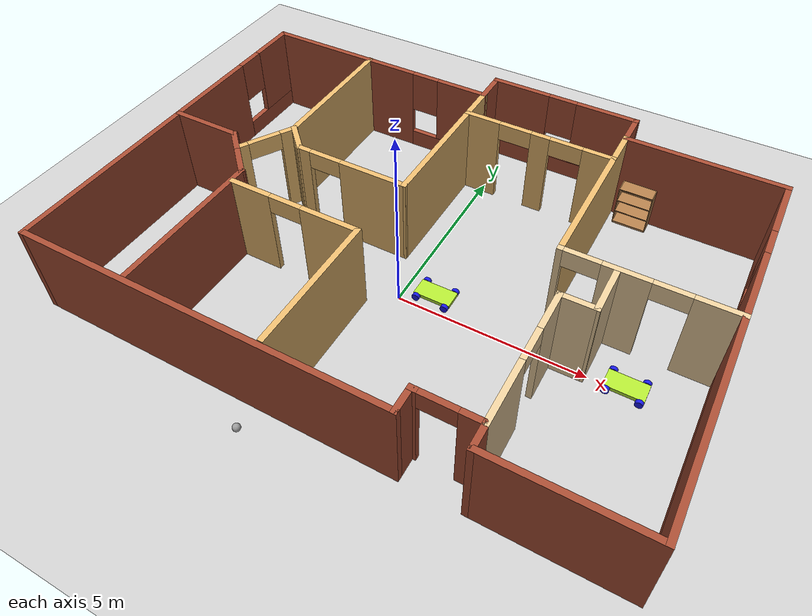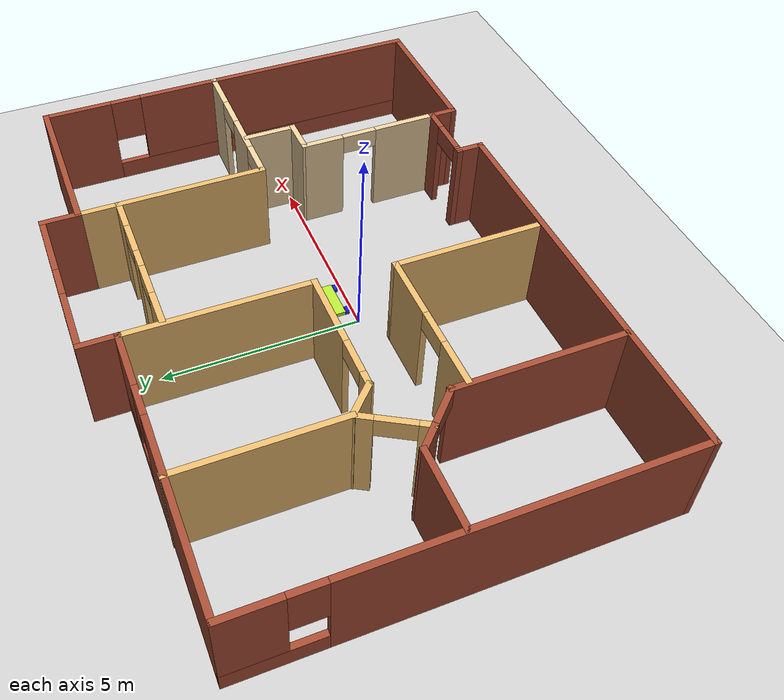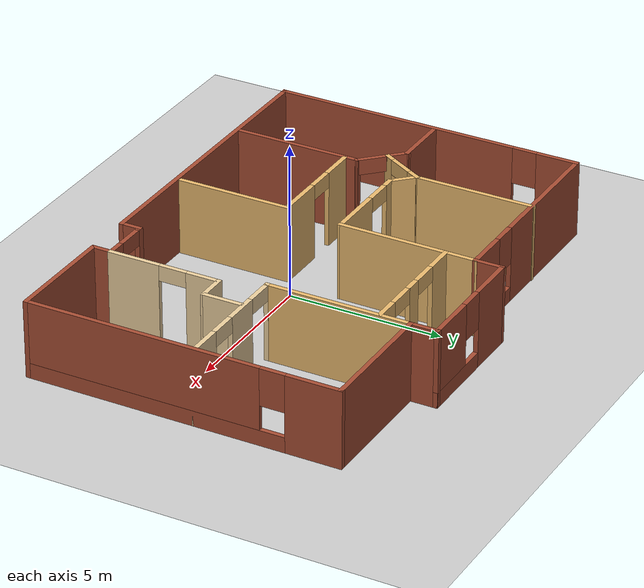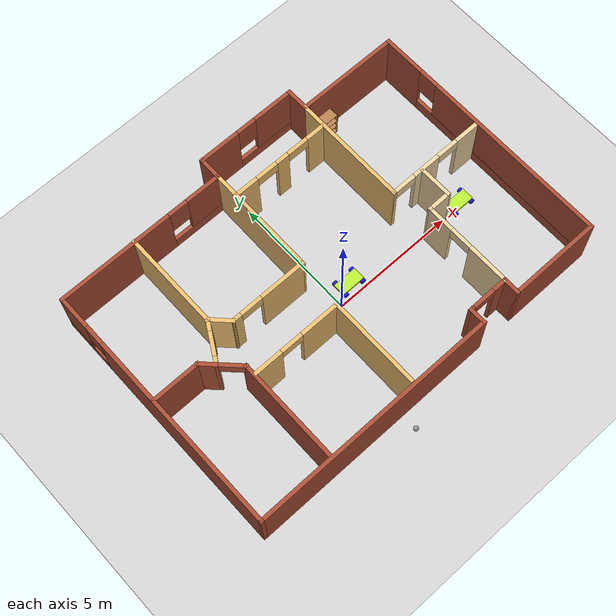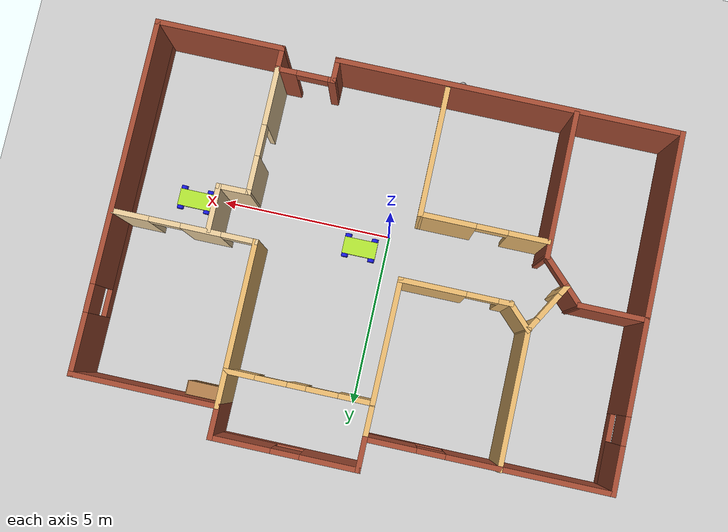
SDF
<sdf version="1.6">
 <world name="default">
  <plugin name="welcomemessage" filename="libwelcomemessage.so"/>
  <light name="sun" type="directional">
   <pose>0 0 10 0 -0 0</pose>
   <diffuse>0.8 0.8 0.8 1</diffuse>
   <specular>0.2 0.2 0.2 1</specular>
   <attenuation>
    <range>1000</range>
    <constant>0.9</constant>
    <linear>0.01</linear>
    <quadratic>0.001</quadratic>
   </attenuation>
   <direction>-0.5 0.1 -0.9</direction>
   <spot><inner_angle>0</inner_angle><outer_angle>0</outer_angle><falloff>0</falloff></spot>
  </light>
  <model name="ground_plane">
   <static>1</static>
   <link name="link">
    <collision name="collision">
     <geometry><plane><normal>0 0 1</normal><size>100 100</size></plane></geometry>
     <surface>
      <contact><collide_bitmask>65535</collide_bitmask></contact>
      <friction><ode><mu>100</mu><mu2>50</mu2></ode></friction>
     </surface>
    </collision>
    <visual name="visual">
     <cast_shadows>0</cast_shadows>
     <geometry><plane><normal>0 0 1</normal><size>100 100</size></plane></geometry>
     <material>
      <script><uri>file://media/materials/scripts/gazebo.material</uri><name>Gazebo/Grey</name></script>
     </material>
    </visual>
   </link>
  </model>
  <gravity>0 0 -9.8</gravity>
  <magnetic_field>6e-06 2.3e-05 -4.2e-05</magnetic_field>
  <atmosphere type="adiabatic"/>
  <physics name="default_physics" default="0" type="ode">
   <max_step_size>0.001</max_step_size>
   <real_time_factor>1</real_time_factor>
   <real_time_update_rate>1000</real_time_update_rate>
  </physics>
  <scene><ambient>0.4 0.4 0.4 1</ambient><background>0.7 0.7 0.7 1</background><shadows>1</shadows></scene>
  <spherical_coordinates>
   <surface_model>EARTH_WGS84</surface_model>
   <latitude_deg>0</latitude_deg>
   <longitude_deg>0</longitude_deg>
   <elevation>0</elevation>
   <heading_deg>0</heading_deg>
  </spherical_coordinates>
  <model name="RobotHouse">
   <pose>0.10736 1.17613 0 0 -0 0</pose>
   <link name="Wall_20">
    <pose>-4.1 4.625 0 0 -0 0</pose>
    <visual name="Wall_20_Visual_0">
     <pose>-1.15251 0 1.25 0 -0 0</pose>
     <geometry><box><size>4.69498 0.15 2.5</size></box></geometry>
     <material>
      <script><uri>file://media/materials/scripts/gazebo.material</uri><name>Gazebo/Bricks</name></script>
      <ambient>1 1 1 1</ambient>
     </material>
     <meta><layer>0</layer></meta>
    </visual>
    <collision name="Wall_20_Collision_0">
     <geometry><box><size>4.69498 0.15 2.5</size></box></geometry>
     <pose>-1.15251 0 1.25 0 -0 0</pose>
    </collision>
    <visual name="Wall_20_Visual_1">
     <pose>2.34749 0 0.25 0 -0 0</pose>
     <geometry><box><size>2.30503 0.15 0.5</size></box></geometry>
     <material>
      <script><uri>file://media/materials/scripts/gazebo.material</uri><name>Gazebo/Bricks</name></script>
      <ambient>1 1 1 1</ambient>
     </material>
     <meta><layer>0</layer></meta>
    </visual>
    <collision name="Wall_20_Collision_1">
     <geometry><box><size>2.30503 0.15 0.5</size></box></geometry>
     <pose>2.34749 0 0.25 0 -0 0</pose>
    </collision>
    <visual name="Wall_20_Visual_2">
     <pose>2.74749 0 1.5 0 -0 0</pose>
     <geometry><box><size>1.50503 0.15 2</size></box></geometry>
     <material>
      <script><uri>file://media/materials/scripts/gazebo.material</uri><name>Gazebo/Bricks</name></script>
      <ambient>1 1 1 1</ambient>
     </material>
     <meta><layer>0</layer></meta>
    </visual>
    <collision name="Wall_20_Collision_2">
     <geometry><box><size>1.50503 0.15 2</size></box></geometry>
     <pose>2.74749 0 1.5 0 -0 0</pose>
    </collision>
    <visual name="Wall_20_Visual_3">
     <pose>1.59498 0 1.9 0 -0 0</pose>
     <geometry><box><size>0.8 0.15 1.2</size></box></geometry>
     <material>
      <script><uri>file://media/materials/scripts/gazebo.material</uri><name>Gazebo/Bricks</name></script>
      <ambient>1 1 1 1</ambient>
     </material>
     <meta><layer>0</layer></meta>
    </visual>
    <collision name="Wall_20_Collision_3">
     <geometry><box><size>0.8 0.15 1.2</size></box></geometry>
     <pose>1.59498 0 1.9 0 -0 0</pose>
    </collision>
   </link>
   <link name="Wall_21">
    <collision name="Wall_21_Collision">
     <geometry><box><size>1 0.15 2.5</size></box></geometry>
     <pose>0 0 1.25 0 -0 0</pose>
    </collision>
    <visual name="Wall_21_Visual">
     <pose>0 0 1.25 0 -0 0</pose>
     <geometry><box><size>1 0.15 2.5</size></box></geometry>
     <material>
      <script><uri>file://media/materials/scripts/gazebo.material</uri><name>Gazebo/Bricks</name></script>
      <ambient>0.913725 0.72549 0.431373 1</ambient>
     </material>
     <meta><layer>0</layer></meta>
    </visual>
    <pose>-0.675 5.05 0 0 -0 1.5708</pose>
   </link>
   <link name="Wall_22">
    <pose>1.375 5.475 0 0 -0 0</pose>
    <visual name="Wall_22_Visual_0">
     <pose>-1.2722 0 1.25 0 -0 0</pose>
     <geometry><box><size>1.70559 0.15 2.5</size></box></geometry>
     <material>
      <script><uri>file://media/materials/scripts/gazebo.material</uri><name>Gazebo/Bricks</name></script>
      <ambient>1 1 1 1</ambient>
     </material>
     <meta><layer>0</layer></meta>
    </visual>
    <collision name="Wall_22_Collision_0">
     <geometry><box><size>1.70559 0.15 2.5</size></box></geometry>
     <pose>-1.2722 0 1.25 0 -0 0</pose>
    </collision>
    <visual name="Wall_22_Visual_1">
     <pose>0.852797 0 0.25 0 -0 0</pose>
     <geometry><box><size>2.54441 0.15 0.5</size></box></geometry>
     <material>
      <script><uri>file://media/materials/scripts/gazebo.material</uri><name>Gazebo/Bricks</name></script>
      <ambient>1 1 1 1</ambient>
     </material>
     <meta><layer>0</layer></meta>
    </visual>
    <collision name="Wall_22_Collision_1">
     <geometry><box><size>2.54441 0.15 0.5</size></box></geometry>
     <pose>0.852797 0 0.25 0 -0 0</pose>
    </collision>
    <visual name="Wall_22_Visual_2">
     <pose>1.2528 0 1.5 0 -0 0</pose>
     <geometry><box><size>1.74441 0.15 2</size></box></geometry>
     <material>
      <script><uri>file://media/materials/scripts/gazebo.material</uri><name>Gazebo/Bricks</name></script>
      <ambient>1 1 1 1</ambient>
     </material>
     <meta><layer>0</layer></meta>
    </visual>
    <collision name="Wall_22_Collision_2">
     <geometry><box><size>1.74441 0.15 2</size></box></geometry>
     <pose>1.2528 0 1.5 0 -0 0</pose>
    </collision>
    <visual name="Wall_22_Visual_3">
     <pose>-0.019407 0 1.9 0 -0 0</pose>
     <geometry><box><size>0.8 0.15 1.2</size></box></geometry>
     <material>
      <script><uri>file://media/materials/scripts/gazebo.material</uri><name>Gazebo/Bricks</name></script>
      <ambient>1 1 1 1</ambient>
     </material>
     <meta><layer>0</layer></meta>
    </visual>
    <collision name="Wall_22_Collision_3">
     <geometry><box><size>0.8 0.15 1.2</size></box></geometry>
     <pose>-0.019407 0 1.9 0 -0 0</pose>
    </collision>
   </link>
   <link name="Wall_23">
    <collision name="Wall_23_Collision">
     <geometry><box><size>1 0.15 2.5</size></box></geometry>
     <pose>0 0 1.25 0 -0 0</pose>
    </collision>
    <visual name="Wall_23_Visual">
     <pose>0 0 1.25 0 -0 0</pose>
     <geometry><box><size>1 0.15 2.5</size></box></geometry>
     <material>
      <script><uri>file://media/materials/scripts/gazebo.material</uri><name>Gazebo/Bricks</name></script>
      <ambient>0.921569 0.807843 0.615686 1</ambient>
     </material>
     <meta><layer>0</layer></meta>
    </visual>
    <pose>3.425 5.05 0 0 -0 -1.5708</pose>
   </link>
   <link name="Wall_24">
    <collision name="Wall_24_Collision">
     <geometry><box><size>4.25 0.15 2.5</size></box></geometry>
     <pose>0 0 1.25 0 -0 0</pose>
    </collision>
    <visual name="Wall_24_Visual">
     <pose>0 0 1.25 0 -0 0</pose>
     <geometry><box><size>4.25 0.15 2.5</size></box></geometry>
     <material>
      <script><uri>file://media/materials/scripts/gazebo.material</uri><name>Gazebo/Bricks</name></script>
      <ambient>0.913725 0.72549 0.431373 1</ambient>
     </material>
     <meta><layer>0</layer></meta>
    </visual>
    <pose>5.475 4.625 0 0 -0 0</pose>
   </link>
   <link name="Wall_25">
    <pose>7.525 -0.425 0 0 -0 -1.5708</pose>
    <visual name="Wall_25_Visual_0">
     <pose>-4.22927 0 1.25 0 -0 0</pose>
     <geometry><box><size>1.79147 0.15 2.5</size></box></geometry>
     <material>
      <script><uri>file://media/materials/scripts/gazebo.material</uri><name>Gazebo/Bricks</name></script>
      <ambient>1 1 1 1</ambient>
     </material>
     <meta><layer>0</layer></meta>
    </visual>
    <collision name="Wall_25_Collision_0">
     <geometry><box><size>1.79147 0.15 2.5</size></box></geometry>
     <pose>-4.22927 0 1.25 0 -0 0</pose>
    </collision>
    <visual name="Wall_25_Visual_1">
     <pose>0.895734 0 0.25 0 -0 0</pose>
     <geometry><box><size>8.45853 0.15 0.5</size></box></geometry>
     <material>
      <script><uri>file://media/materials/scripts/gazebo.material</uri><name>Gazebo/Bricks</name></script>
      <ambient>1 1 1 1</ambient>
     </material>
     <meta><layer>0</layer></meta>
    </visual>
    <collision name="Wall_25_Collision_1">
     <geometry><box><size>8.45853 0.15 0.5</size></box></geometry>
     <pose>0.895734 0 0.25 0 -0 0</pose>
    </collision>
    <visual name="Wall_25_Visual_2">
     <pose>1.29573 0 1.5 0 -0 0</pose>
     <geometry><box><size>7.65853 0.15 2</size></box></geometry>
     <material>
      <script><uri>file://media/materials/scripts/gazebo.material</uri><name>Gazebo/Bricks</name></script>
      <ambient>1 1 1 1</ambient>
     </material>
     <meta><layer>0</layer></meta>
    </visual>
    <collision name="Wall_25_Collision_2">
     <geometry><box><size>7.65853 0.15 2</size></box></geometry>
     <pose>1.29573 0 1.5 0 -0 0</pose>
    </collision>
    <visual name="Wall_25_Visual_3">
     <pose>-2.93353 0 1.9 0 -0 0</pose>
     <geometry><box><size>0.8 0.15 1.2</size></box></geometry>
     <material>
      <script><uri>file://media/materials/scripts/gazebo.material</uri><name>Gazebo/Bricks</name></script>
      <ambient>1 1 1 1</ambient>
     </material>
     <meta><layer>0</layer></meta>
    </visual>
    <collision name="Wall_25_Collision_3">
     <geometry><box><size>0.8 0.15 1.2</size></box></geometry>
     <pose>-2.93353 0 1.9 0 -0 0</pose>
    </collision>
   </link>
   <link name="Wall_26">
    <collision name="Wall_26_Collision">
     <geometry><box><size>3.75 0.15 2.5</size></box></geometry>
     <pose>0 0 1.25 0 -0 0</pose>
    </collision>
    <visual name="Wall_26_Visual">
     <pose>0 0 1.25 0 -0 0</pose>
     <geometry><box><size>3.75 0.15 2.5</size></box></geometry>
     <material>
      <script><uri>file://media/materials/scripts/gazebo.material</uri><name>Gazebo/Bricks</name></script>
      <ambient>1 1 1 1</ambient>
     </material>
     <meta><layer>0</layer></meta>
    </visual>
    <pose>5.725 -5.475 0 0 -0 3.14159</pose>
   </link>
   <link name="Wall_27">
    <collision name="Wall_27_Collision">
     <geometry><box><size>0.75 0.15 2.5</size></box></geometry>
     <pose>0 0 1.25 0 -0 0</pose>
    </collision>
    <visual name="Wall_27_Visual">
     <pose>0 0 1.25 0 -0 0</pose>
     <geometry><box><size>0.75 0.15 2.5</size></box></geometry>
     <material>
      <script><uri>file://media/materials/scripts/gazebo.material</uri><name>Gazebo/Bricks</name></script>
      <ambient>1 1 1 1</ambient>
     </material>
     <meta><layer>0</layer></meta>
    </visual>
    <pose>3.925 -5.175 0 0 -0 1.5708</pose>
   </link>
   <link name="Wall_28">
    <pose>3.125 -4.875 0 0 -0 3.14159</pose>
    <visual name="Wall_28_Visual_0">
     <pose>-0.56282 0 1.25 0 -0 0</pose>
     <geometry><box><size>0.62436 0.15 2.5</size></box></geometry>
     <material>
      <script><uri>file://media/materials/scripts/gazebo.material</uri><name>Gazebo/Bricks</name></script>
      <ambient>1 1 1 1</ambient>
     </material>
     <meta><layer>0</layer></meta>
    </visual>
    <collision name="Wall_28_Collision_0">
     <geometry><box><size>0.62436 0.15 2.5</size></box></geometry>
     <pose>-0.56282 0 1.25 0 -0 0</pose>
    </collision>
    <visual name="Wall_28_Visual_1">
     <pose>0.76218 0 1.25 0 -0 0</pose>
     <geometry><box><size>0.22564 0.15 2.5</size></box></geometry>
     <material>
      <script><uri>file://media/materials/scripts/gazebo.material</uri><name>Gazebo/Bricks</name></script>
      <ambient>1 1 1 1</ambient>
     </material>
     <meta><layer>0</layer></meta>
    </visual>
    <collision name="Wall_28_Collision_1">
     <geometry><box><size>0.22564 0.15 2.5</size></box></geometry>
     <pose>0.76218 0 1.25 0 -0 0</pose>
    </collision>
    <visual name="Wall_28_Visual_2">
     <pose>0.19936 0 2.25 0 -0 0</pose>
     <geometry><box><size>0.9 0.15 0.5</size></box></geometry>
     <material>
      <script><uri>file://media/materials/scripts/gazebo.material</uri><name>Gazebo/Bricks</name></script>
      <ambient>1 1 1 1</ambient>
     </material>
     <meta><layer>0</layer></meta>
    </visual>
    <collision name="Wall_28_Collision_2">
     <geometry><box><size>0.9 0.15 0.5</size></box></geometry>
     <pose>0.19936 0 2.25 0 -0 0</pose>
    </collision>
   </link>
   <link name="Wall_29">
    <collision name="Wall_29_Collision">
     <geometry><box><size>0.75 0.15 2.5</size></box></geometry>
     <pose>0 0 1.25 0 -0 0</pose>
    </collision>
    <visual name="Wall_29_Visual">
     <pose>0 0 1.25 0 -0 0</pose>
     <geometry><box><size>0.75 0.15 2.5</size></box></geometry>
     <material>
      <script><uri>file://media/materials/scripts/gazebo.material</uri><name>Gazebo/Bricks</name></script>
      <ambient>1 1 1 1</ambient>
     </material>
     <meta><layer>0</layer></meta>
    </visual>
    <pose>2.325 -5.175 0 0 -0 -1.5708</pose>
   </link>
   <link name="Wall_30">
    <collision name="Wall_30_Collision">
     <geometry><box><size>10 0.15 2.5</size></box></geometry>
     <pose>0 0 1.25 0 -0 0</pose>
    </collision>
    <visual name="Wall_30_Visual">
     <pose>0 0 1.25 0 -0 0</pose>
     <geometry><box><size>10 0.15 2.5</size></box></geometry>
     <material>
      <script><uri>file://media/materials/scripts/gazebo.material</uri><name>Gazebo/Bricks</name></script>
      <ambient>1 1 1 1</ambient>
     </material>
     <meta><layer>0</layer></meta>
    </visual>
    <pose>-2.6 -5.475 0 0 -0 3.14159</pose>
   </link>
   <link name="Wall_31">
    <pose>-7.525 -0.425 0 0 -0 1.5708</pose>
    <visual name="Wall_31_Visual_0">
     <pose>-1.0946 0 1.25 0 -0 0</pose>
     <geometry><box><size>8.0608 0.15 2.5</size></box></geometry>
     <material>
      <script><uri>file://media/materials/scripts/gazebo.material</uri><name>Gazebo/Bricks</name></script>
      <ambient>1 1 1 1</ambient>
     </material>
     <meta><layer>0</layer></meta>
    </visual>
    <collision name="Wall_31_Collision_0">
     <geometry><box><size>8.0608 0.15 2.5</size></box></geometry>
     <pose>-1.0946 0 1.25 0 -0 0</pose>
    </collision>
    <visual name="Wall_31_Visual_1">
     <pose>4.0304 0 0.25 0 -0 0</pose>
     <geometry><box><size>2.1892 0.15 0.5</size></box></geometry>
     <material>
      <script><uri>file://media/materials/scripts/gazebo.material</uri><name>Gazebo/Bricks</name></script>
      <ambient>1 1 1 1</ambient>
     </material>
     <meta><layer>0</layer></meta>
    </visual>
    <collision name="Wall_31_Collision_1">
     <geometry><box><size>2.1892 0.15 0.5</size></box></geometry>
     <pose>4.0304 0 0.25 0 -0 0</pose>
    </collision>
    <visual name="Wall_31_Visual_2">
     <pose>4.4304 0 1.5 0 -0 0</pose>
     <geometry><box><size>1.3892 0.15 2</size></box></geometry>
     <material>
      <script><uri>file://media/materials/scripts/gazebo.material</uri><name>Gazebo/Bricks</name></script>
      <ambient>1 1 1 1</ambient>
     </material>
     <meta><layer>0</layer></meta>
    </visual>
    <collision name="Wall_31_Collision_2">
     <geometry><box><size>1.3892 0.15 2</size></box></geometry>
     <pose>4.4304 0 1.5 0 -0 0</pose>
    </collision>
    <visual name="Wall_31_Visual_3">
     <pose>3.3358 0 1.9 0 -0 0</pose>
     <geometry><box><size>0.8 0.15 1.2</size></box></geometry>
     <material>
      <script><uri>file://media/materials/scripts/gazebo.material</uri><name>Gazebo/Bricks</name></script>
      <ambient>1 1 1 1</ambient>
     </material>
     <meta><layer>0</layer></meta>
    </visual>
    <collision name="Wall_31_Collision_3">
     <geometry><box><size>0.8 0.15 1.2</size></box></geometry>
     <pose>3.3358 0 1.9 0 -0 0</pose>
    </collision>
   </link>
   <link name="Wall_33">
    <collision name="Wall_33_Collision">
     <geometry><box><size>2 0.15 2.5</size></box></geometry>
     <pose>0 0 1.25 0 -0 0</pose>
    </collision>
    <visual name="Wall_33_Visual">
     <pose>0 0 1.25 0 -0 0</pose>
     <geometry><box><size>2 0.15 2.5</size></box></geometry>
     <material>
      <script><uri>file://media/materials/scripts/gazebo.material</uri><name>Gazebo/Bricks</name></script>
      <ambient>0.921569 0.807843 0.615686 1</ambient>
     </material>
     <meta><layer>0</layer></meta>
    </visual>
    <pose>-6.57641 -0.166944 0 0 -0 0</pose>
   </link>
   <link name="Wall_34">
    <pose>-5.08572 -0.732629 0 0 -0 -0.785398</pose>
    <visual name="Wall_34_Visual_0">
     <pose>-0.497781 0 1.25 0 -0 0</pose>
     <geometry><box><size>0.754439 0.15 2.5</size></box></geometry>
     <material>
      <script><uri>file://media/materials/scripts/gazebo.material</uri><name>Gazebo/Bricks</name></script>
      <ambient>1 1 1 1</ambient>
     </material>
     <meta><layer>0</layer></meta>
    </visual>
    <collision name="Wall_34_Collision_0">
     <geometry><box><size>0.754439 0.15 2.5</size></box></geometry>
     <pose>-0.497781 0 1.25 0 -0 0</pose>
    </collision>
    <visual name="Wall_34_Visual_1">
     <pose>0.827219 0 1.25 0 -0 0</pose>
     <geometry><box><size>0.095561 0.15 2.5</size></box></geometry>
     <material>
      <script><uri>file://media/materials/scripts/gazebo.material</uri><name>Gazebo/Bricks</name></script>
      <ambient>1 1 1 1</ambient>
     </material>
     <meta><layer>0</layer></meta>
    </visual>
    <collision name="Wall_34_Collision_1">
     <geometry><box><size>0.095561 0.15 2.5</size></box></geometry>
     <pose>0.827219 0 1.25 0 -0 0</pose>
    </collision>
    <visual name="Wall_34_Visual_2">
     <pose>0.329439 0 2.25 0 -0 0</pose>
     <geometry><box><size>0.9 0.15 0.5</size></box></geometry>
     <material>
      <script><uri>file://media/materials/scripts/gazebo.material</uri><name>Gazebo/Bricks</name></script>
      <ambient>1 1 1 1</ambient>
     </material>
     <meta><layer>0</layer></meta>
    </visual>
    <collision name="Wall_34_Collision_2">
     <geometry><box><size>0.9 0.15 0.5</size></box></geometry>
     <pose>0.329439 0 2.25 0 -0 0</pose>
    </collision>
   </link>
   <link name="Wall_35">
    <collision name="Wall_35_Collision">
     <geometry><box><size>4.25 0.15 2.5</size></box></geometry>
     <pose>0 0 1.25 0 -0 0</pose>
    </collision>
    <visual name="Wall_35_Visual">
     <pose>0 0 1.25 0 -0 0</pose>
     <geometry><box><size>4.25 0.15 2.5</size></box></geometry>
     <material>
      <script><uri>file://media/materials/scripts/gazebo.material</uri><name>Gazebo/Bricks</name></script>
      <ambient>1 1 1 1</ambient>
     </material>
     <meta><layer>0</layer></meta>
    </visual>
    <pose>-4.52004 -3.34831 0 0 -0 -1.5708</pose>
   </link>
   <link name="Wall_38">
    <collision name="Wall_38_Collision">
     <geometry><box><size>4 0.15 2.5</size></box></geometry>
     <pose>0 0 1.25 0 -0 0</pose>
    </collision>
    <visual name="Wall_38_Visual">
     <pose>0 0 1.25 0 -0 0</pose>
     <geometry><box><size>4 0.15 2.5</size></box></geometry>
     <material>
      <script><uri>file://media/materials/scripts/gazebo.material</uri><name>Gazebo/Grey</name></script>
      <ambient>0.913725 0.72549 0.431373 1</ambient>
     </material>
     <meta><layer>0</layer></meta>
    </visual>
    <pose>-4.40567 2.71782 0 0 -0 -1.5708</pose>
   </link>
   <link name="Wall_39">
    <pose>-4.80567 0.100003 0 0 -0 -2.0944</pose>
    <visual name="Wall_39_Visual_0">
     <pose>-0.632046 0 1.25 0 -0 0</pose>
     <geometry><box><size>0.485909 0.15 2.5</size></box></geometry>
     <material>
      <script><uri>file://media/materials/scripts/gazebo.material</uri><name>Gazebo/Grey</name></script>
      <ambient>0.913725 0.72549 0.431373 1</ambient>
     </material>
     <meta><layer>0</layer></meta>
    </visual>
    <collision name="Wall_39_Collision_0">
     <geometry><box><size>0.485909 0.15 2.5</size></box></geometry>
     <pose>-0.632046 0 1.25 0 -0 0</pose>
    </collision>
    <visual name="Wall_39_Visual_1">
     <pose>0.692954 0 1.25 0 -0 0</pose>
     <geometry><box><size>0.364091 0.15 2.5</size></box></geometry>
     <material>
      <script><uri>file://media/materials/scripts/gazebo.material</uri><name>Gazebo/Grey</name></script>
      <ambient>0.913725 0.72549 0.431373 1</ambient>
     </material>
     <meta><layer>0</layer></meta>
    </visual>
    <collision name="Wall_39_Collision_1">
     <geometry><box><size>0.364091 0.15 2.5</size></box></geometry>
     <pose>0.692954 0 1.25 0 -0 0</pose>
    </collision>
    <visual name="Wall_39_Visual_2">
     <pose>0.060909 0 2.25 0 -0 0</pose>
     <geometry><box><size>0.9 0.15 0.5</size></box></geometry>
     <material>
      <script><uri>file://media/materials/scripts/gazebo.material</uri><name>Gazebo/Grey</name></script>
      <ambient>0.913725 0.72549 0.431373 1</ambient>
     </material>
     <meta><layer>0</layer></meta>
    </visual>
    <collision name="Wall_39_Collision_2">
     <geometry><box><size>0.9 0.15 0.5</size></box></geometry>
     <pose>0.060909 0 2.25 0 -0 0</pose>
    </collision>
   </link>
   <link name="Wall_41">
    <collision name="Wall_41_Collision">
     <geometry><box><size>1 0.15 2.5</size></box></geometry>
     <pose>0 0 1.25 0 -0 0</pose>
    </collision>
    <visual name="Wall_41_Visual">
     <pose>0 0 1.25 0 -0 0</pose>
     <geometry><box><size>1 0.15 2.5</size></box></geometry>
     <material>
      <script><uri>file://media/materials/scripts/gazebo.material</uri><name>Gazebo/Grey</name></script>
      <ambient>0.913725 0.72549 0.431373 1</ambient>
     </material>
     <meta><layer>0</layer></meta>
    </visual>
    <pose>-4.10515 0.492303 0 0 -0 -0.785398</pose>
   </link>
   <link name="Wall_42">
    <pose>-2.25463 0.191783 0 0 -0 0</pose>
    <visual name="Wall_42_Visual_0">
     <pose>-1.41412 0 1.25 0 -0 0</pose>
     <geometry><box><size>0.421763 0.15 2.5</size></box></geometry>
     <material>
      <script><uri>file://media/materials/scripts/gazebo.material</uri><name>Gazebo/Grey</name></script>
      <ambient>0.913725 0.72549 0.431373 1</ambient>
     </material>
     <meta><layer>0</layer></meta>
    </visual>
    <collision name="Wall_42_Collision_0">
     <geometry><box><size>0.421763 0.15 2.5</size></box></geometry>
     <pose>-1.41412 0 1.25 0 -0 0</pose>
    </collision>
    <visual name="Wall_42_Visual_1">
     <pose>0.660881 0 1.25 0 -0 0</pose>
     <geometry><box><size>1.92824 0.15 2.5</size></box></geometry>
     <material>
      <script><uri>file://media/materials/scripts/gazebo.material</uri><name>Gazebo/Grey</name></script>
      <ambient>0.913725 0.72549 0.431373 1</ambient>
     </material>
     <meta><layer>0</layer></meta>
    </visual>
    <collision name="Wall_42_Collision_1">
     <geometry><box><size>1.92824 0.15 2.5</size></box></geometry>
     <pose>0.660881 0 1.25 0 -0 0</pose>
    </collision>
    <visual name="Wall_42_Visual_2">
     <pose>-0.753237 0 2.25 0 -0 0</pose>
     <geometry><box><size>0.9 0.15 0.5</size></box></geometry>
     <material>
      <script><uri>file://media/materials/scripts/gazebo.material</uri><name>Gazebo/Grey</name></script>
      <ambient>0.913725 0.72549 0.431373 1</ambient>
     </material>
     <meta><layer>0</layer></meta>
    </visual>
    <collision name="Wall_42_Collision_2">
     <geometry><box><size>0.9 0.15 0.5</size></box></geometry>
     <pose>-0.753237 0 2.25 0 -0 0</pose>
    </collision>
   </link>
   <link name="Wall_43">
    <collision name="Wall_43_Collision">
     <geometry><box><size>4.58332 0.15 2.5</size></box></geometry>
     <pose>0 0 1.25 0 -0 0</pose>
    </collision>
    <visual name="Wall_43_Visual">
     <pose>0 0 1.25 0 -0 0</pose>
     <geometry><box><size>4.58332 0.15 2.5</size></box></geometry>
     <material>
      <script><uri>file://media/materials/scripts/gazebo.material</uri><name>Gazebo/Grey</name></script>
      <ambient>0.913725 0.72549 0.431373 1</ambient>
     </material>
     <meta><layer>0</layer></meta>
    </visual>
    <pose>-0.689813 2.40839 0 0 -0 1.56411</pose>
   </link>
   <link name="Wall_45">
    <collision name="Wall_45_Collision">
     <geometry><box><size>4.75 0.15 2.5</size></box></geometry>
     <pose>0 0 1.25 0 -0 0</pose>
    </collision>
    <visual name="Wall_45_Visual">
     <pose>0 0 1.25 0 -0 0</pose>
     <geometry><box><size>4.75 0.15 2.5</size></box></geometry>
     <material>
      <script><uri>file://media/materials/scripts/gazebo.material</uri><name>Gazebo/Grey</name></script>
      <ambient>0.913725 0.72549 0.431373 1</ambient>
     </material>
     <meta><layer>0</layer></meta>
    </visual>
    <pose>3.425 2.325 0 0 -0 -1.5708</pose>
   </link>
   <link name="Wall_46">
    <pose>5.475 0.025 0 0 -0 0</pose>
    <visual name="Wall_46_Visual_0">
     <pose>-2.04928 0 1.25 0 -0 0</pose>
     <geometry><box><size>0.151432 0.15 2.5</size></box></geometry>
     <material>
      <script><uri>file://media/materials/scripts/gazebo.material</uri><name>Gazebo/Grey</name></script>
      <ambient>0.921569 0.807843 0.615686 1</ambient>
     </material>
     <meta><layer>0</layer></meta>
    </visual>
    <collision name="Wall_46_Collision_0">
     <geometry><box><size>0.151432 0.15 2.5</size></box></geometry>
     <pose>-2.04928 0 1.25 0 -0 0</pose>
    </collision>
    <visual name="Wall_46_Visual_1">
     <pose>-0.497776 0 1.25 0 -0 0</pose>
     <geometry><box><size>1.15159 0.15 2.5</size></box></geometry>
     <material>
      <script><uri>file://media/materials/scripts/gazebo.material</uri><name>Gazebo/Grey</name></script>
      <ambient>0.921569 0.807843 0.615686 1</ambient>
     </material>
     <meta><layer>0</layer></meta>
    </visual>
    <collision name="Wall_46_Collision_1">
     <geometry><box><size>1.15159 0.15 2.5</size></box></geometry>
     <pose>-0.497776 0 1.25 0 -0 0</pose>
    </collision>
    <visual name="Wall_46_Visual_2">
     <pose>1.55151 0 1.25 0 -0 0</pose>
     <geometry><box><size>1.14698 0.15 2.5</size></box></geometry>
     <material>
      <script><uri>file://media/materials/scripts/gazebo.material</uri><name>Gazebo/Grey</name></script>
      <ambient>0.921569 0.807843 0.615686 1</ambient>
     </material>
     <meta><layer>0</layer></meta>
    </visual>
    <collision name="Wall_46_Collision_2">
     <geometry><box><size>1.14698 0.15 2.5</size></box></geometry>
     <pose>1.55151 0 1.25 0 -0 0</pose>
    </collision>
    <visual name="Wall_46_Visual_3">
     <pose>-1.52357 0 2.25 0 -0 0</pose>
     <geometry><box><size>0.9 0.15 0.5</size></box></geometry>
     <material>
      <script><uri>file://media/materials/scripts/gazebo.material</uri><name>Gazebo/Grey</name></script>
      <ambient>0.921569 0.807843 0.615686 1</ambient>
     </material>
     <meta><layer>0</layer></meta>
    </visual>
    <collision name="Wall_46_Collision_3">
     <geometry><box><size>0.9 0.15 0.5</size></box></geometry>
     <pose>-1.52357 0 2.25 0 -0 0</pose>
    </collision>
    <visual name="Wall_46_Visual_4">
     <pose>0.528017 0 2.25 0 -0 0</pose>
     <geometry><box><size>0.9 0.15 0.5</size></box></geometry>
     <material>
      <script><uri>file://media/materials/scripts/gazebo.material</uri><name>Gazebo/Grey</name></script>
      <ambient>0.921569 0.807843 0.615686 1</ambient>
     </material>
     <meta><layer>0</layer></meta>
    </visual>
    <collision name="Wall_46_Collision_4">
     <geometry><box><size>0.9 0.15 0.5</size></box></geometry>
     <pose>0.528017 0 2.25 0 -0 0</pose>
    </collision>
   </link>
   <link name="Wall_48">
    <pose>1.36972 3.64589 0 0 -0 0</pose>
    <visual name="Wall_48_Visual_0">
     <pose>-1.60573 0 1.25 0 -0 0</pose>
     <geometry><box><size>1.03854 0.15 2.5</size></box></geometry>
     <material>
      <script><uri>file://media/materials/scripts/gazebo.material</uri><name>Gazebo/Grey</name></script>
      <ambient>0.913725 0.72549 0.431373 1</ambient>
     </material>
     <meta><layer>0</layer></meta>
    </visual>
    <collision name="Wall_48_Collision_0">
     <geometry><box><size>1.03854 0.15 2.5</size></box></geometry>
     <pose>-1.60573 0 1.25 0 -0 0</pose>
    </collision>
    <visual name="Wall_48_Visual_1">
     <pose>0.077576 0 1.25 0 -0 0</pose>
     <geometry><box><size>0.528064 0.15 2.5</size></box></geometry>
     <material>
      <script><uri>file://media/materials/scripts/gazebo.material</uri><name>Gazebo/Grey</name></script>
      <ambient>0.913725 0.72549 0.431373 1</ambient>
     </material>
     <meta><layer>0</layer></meta>
    </visual>
    <collision name="Wall_48_Collision_1">
     <geometry><box><size>0.528064 0.15 2.5</size></box></geometry>
     <pose>0.077576 0 1.25 0 -0 0</pose>
    </collision>
    <visual name="Wall_48_Visual_2">
     <pose>1.6833 0 1.25 0 -0 0</pose>
     <geometry><box><size>0.883392 0.15 2.5</size></box></geometry>
     <material>
      <script><uri>file://media/materials/scripts/gazebo.material</uri><name>Gazebo/Grey</name></script>
      <ambient>0.913725 0.72549 0.431373 1</ambient>
     </material>
     <meta><layer>0</layer></meta>
    </visual>
    <collision name="Wall_48_Collision_2">
     <geometry><box><size>0.883392 0.15 2.5</size></box></geometry>
     <pose>1.6833 0 1.25 0 -0 0</pose>
    </collision>
    <visual name="Wall_48_Visual_3">
     <pose>-0.636456 0 2.25 0 -0 0</pose>
     <geometry><box><size>0.9 0.15 0.5</size></box></geometry>
     <material>
      <script><uri>file://media/materials/scripts/gazebo.material</uri><name>Gazebo/Grey</name></script>
      <ambient>0.913725 0.72549 0.431373 1</ambient>
     </material>
     <meta><layer>0</layer></meta>
    </visual>
    <collision name="Wall_48_Collision_3">
     <geometry><box><size>0.9 0.15 0.5</size></box></geometry>
     <pose>-0.636456 0 2.25 0 -0 0</pose>
    </collision>
    <visual name="Wall_48_Visual_4">
     <pose>0.791608 0 2.25 0 -0 0</pose>
     <geometry><box><size>0.9 0.15 0.5</size></box></geometry>
     <material>
      <script><uri>file://media/materials/scripts/gazebo.material</uri><name>Gazebo/Grey</name></script>
      <ambient>0.913725 0.72549 0.431373 1</ambient>
     </material>
     <meta><layer>0</layer></meta>
    </visual>
    <collision name="Wall_48_Collision_4">
     <geometry><box><size>0.9 0.15 0.5</size></box></geometry>
     <pose>0.791608 0 2.25 0 -0 0</pose>
    </collision>
   </link>
   <link name="Wall_50">
    <pose>-2.65814 -1.70607 0 0 -0 0</pose>
    <visual name="Wall_50_Visual_0">
     <pose>-1.27702 0 1.25 0 -0 0</pose>
     <geometry><box><size>1.19596 0.15 2.5</size></box></geometry>
     <material>
      <script><uri>file://media/materials/scripts/gazebo.material</uri><name>Gazebo/Grey</name></script>
      <ambient>0.913725 0.72549 0.431373 1</ambient>
     </material>
     <meta><layer>0</layer></meta>
    </visual>
    <collision name="Wall_50_Collision_0">
     <geometry><box><size>1.19596 0.15 2.5</size></box></geometry>
     <pose>-1.27702 0 1.25 0 -0 0</pose>
    </collision>
    <visual name="Wall_50_Visual_1">
     <pose>1.04798 0 1.25 0 -0 0</pose>
     <geometry><box><size>1.65404 0.15 2.5</size></box></geometry>
     <material>
      <script><uri>file://media/materials/scripts/gazebo.material</uri><name>Gazebo/Grey</name></script>
      <ambient>0.913725 0.72549 0.431373 1</ambient>
     </material>
     <meta><layer>0</layer></meta>
    </visual>
    <collision name="Wall_50_Collision_1">
     <geometry><box><size>1.65404 0.15 2.5</size></box></geometry>
     <pose>1.04798 0 1.25 0 -0 0</pose>
    </collision>
    <visual name="Wall_50_Visual_2">
     <pose>-0.229045 0 2.25 0 -0 0</pose>
     <geometry><box><size>0.9 0.15 0.5</size></box></geometry>
     <material>
      <script><uri>file://media/materials/scripts/gazebo.material</uri><name>Gazebo/Grey</name></script>
      <ambient>0.913725 0.72549 0.431373 1</ambient>
     </material>
     <meta><layer>0</layer></meta>
    </visual>
    <collision name="Wall_50_Collision_2">
     <geometry><box><size>0.9 0.15 0.5</size></box></geometry>
     <pose>-0.229045 0 2.25 0 -0 0</pose>
    </collision>
   </link>
   <link name="Wall_51">
    <collision name="Wall_51_Collision">
     <geometry><box><size>3.75 0.15 2.5</size></box></geometry>
     <pose>0 0 1.25 0 -0 0</pose>
    </collision>
    <visual name="Wall_51_Visual">
     <pose>0 0 1.25 0 -0 0</pose>
     <geometry><box><size>3.75 0.15 2.5</size></box></geometry>
     <material>
      <script><uri>file://media/materials/scripts/gazebo.material</uri><name>Gazebo/Grey</name></script>
      <ambient>0.913725 0.72549 0.431373 1</ambient>
     </material>
     <meta><layer>0</layer></meta>
    </visual>
    <pose>-0.858137 -3.50607 0 0 -0 -1.5708</pose>
   </link>
   <link name="Wall_53">
    <pose>3.925 -3.08157 0 0 -0 1.5708</pose>
    <visual name="Wall_53_Visual_0">
     <pose>-1.00909 0 1.25 0 -0 0</pose>
     <geometry><box><size>1.71866 0.15 2.5</size></box></geometry>
     <material>
      <script><uri>file://media/materials/scripts/gazebo.material</uri><name>Gazebo/Grey</name></script>
      <ambient>0.921569 0.807843 0.615686 1</ambient>
     </material>
     <meta><layer>0</layer></meta>
    </visual>
    <collision name="Wall_53_Collision_0">
     <geometry><box><size>1.71866 0.15 2.5</size></box></geometry>
     <pose>-1.00909 0 1.25 0 -0 0</pose>
    </collision>
    <visual name="Wall_53_Visual_1">
     <pose>1.30933 0 1.25 0 -0 0</pose>
     <geometry><box><size>1.11819 0.15 2.5</size></box></geometry>
     <material>
      <script><uri>file://media/materials/scripts/gazebo.material</uri><name>Gazebo/Grey</name></script>
      <ambient>0.921569 0.807843 0.615686 1</ambient>
     </material>
     <meta><layer>0</layer></meta>
    </visual>
    <collision name="Wall_53_Collision_1">
     <geometry><box><size>1.11819 0.15 2.5</size></box></geometry>
     <pose>1.30933 0 1.25 0 -0 0</pose>
    </collision>
    <visual name="Wall_53_Visual_2">
     <pose>0.300238 0 2.25 0 -0 0</pose>
     <geometry><box><size>0.9 0.15 0.5</size></box></geometry>
     <material>
      <script><uri>file://media/materials/scripts/gazebo.material</uri><name>Gazebo/Grey</name></script>
      <ambient>0.921569 0.807843 0.615686 1</ambient>
     </material>
     <meta><layer>0</layer></meta>
    </visual>
    <collision name="Wall_53_Collision_2">
     <geometry><box><size>0.9 0.15 0.5</size></box></geometry>
     <pose>0.300238 0 2.25 0 -0 0</pose>
    </collision>
   </link>
   <link name="Wall_54">
    <collision name="Wall_54_Collision">
     <geometry><box><size>1 0.15 2.5</size></box></geometry>
     <pose>0 0 1.25 0 -0 0</pose>
    </collision>
    <visual name="Wall_54_Visual">
     <pose>0 0 1.25 0 -0 0</pose>
     <geometry><box><size>1 0.15 2.5</size></box></geometry>
     <material>
      <script><uri>file://media/materials/scripts/gazebo.material</uri><name>Gazebo/Grey</name></script>
      <ambient>0.921569 0.807843 0.615686 1</ambient>
     </material>
     <meta><layer>0</layer></meta>
    </visual>
    <pose>4.35 -1.27829 0 0 -0 0.007735</pose>
   </link>
   <link name="Wall_59">
    <collision name="Wall_59_Collision">
     <geometry><box><size>1.4 0.15 2.5</size></box></geometry>
     <pose>0 0 1.25 0 -0 0</pose>
    </collision>
    <visual name="Wall_59_Visual">
     <pose>0 0 1.25 0 -0 0</pose>
     <geometry><box><size>1.4 0.15 2.5</size></box></geometry>
     <material>
      <script><uri>file://media/materials/scripts/gazebo.material</uri><name>Gazebo/Grey</name></script>
      <ambient>0.921569 0.807843 0.615686 1</ambient>
     </material>
     <meta><layer>0</layer></meta>
    </visual>
    <pose>4.775 -0.65 0 0 -0 1.5708</pose>
   </link>
   <static>1</static>
  </model>
  <model name="mymobilerobot_0">
   <link name="link_0">
    <inertial>
     <mass>1</mass>
     <inertia>
      <ixx>0.166667</ixx>
      <ixy>0</ixy>
      <ixz>0</ixz>
      <iyy>0.166667</iyy>
      <iyz>0</iyz>
      <izz>0.166667</izz>
     </inertia>
    </inertial>
    <pose>-0 -0.003 -0.2 0 -0 0</pose>
    <visual name="visual">
     <geometry><box><size>1 0.5 0.1</size></box></geometry>
     <material>
      <lighting>1</lighting>
      <script><uri>file://media/materials/scripts/gazebo.material</uri><name>Gazebo/Grey</name></script>
      <shader type="pixel"><normal_map>__default__</normal_map></shader>
      <ambient>0.7 0.9 0.2 1</ambient>
      <diffuse>0.7 0.7 0.7 1</diffuse>
      <specular>0.01 0.01 0.01 1</specular>
      <emissive>0 0 0 1</emissive>
     </material>
    </visual>
    <collision name="collision">
     <geometry><box><size>1 0.5 0.1</size></box></geometry>
     <surface>
      <friction>
       <ode><mu>1</mu><mu2>1</mu2><fdir1>0 0 0</fdir1><slip1>0</slip1><slip2>0</slip2></ode>
       <torsional>
        <coefficient>1</coefficient>
        <patch_radius>0</patch_radius>
        <surface_radius>0</surface_radius>
        <use_patch_radius>1</use_patch_radius>
        <ode><slip>0</slip></ode>
       </torsional>
      </friction>
      <bounce><restitution_coefficient>0</restitution_coefficient><threshold>1e+06</threshold></bounce>
      <contact>
       <collide_without_contact>0</collide_without_contact>
       <collide_without_contact_bitmask>1</collide_without_contact_bitmask>
       <collide_bitmask>1</collide_bitmask>
       <ode>
        <soft_cfm>0</soft_cfm>
        <soft_erp>0.2</soft_erp>
        <kp>1e+13</kp>
        <kd>1</kd>
        <max_vel>0.01</max_vel>
        <min_depth>0</min_depth>
       </ode>
       <bullet>
        <split_impulse>1</split_impulse>
        <split_impulse_penetration_threshold>-0.01</split_impulse_penetration_threshold>
        <soft_cfm>0</soft_cfm>
        <soft_erp>0.2</soft_erp>
        <kp>1e+13</kp>
        <kd>1</kd>
       </bullet>
      </contact>
     </surface>
    </collision>
   </link>
   <link name="link_1">
    <inertial>
     <mass>1</mass>
     <inertia><ixx>0.145833</ixx><ixy>0</ixy><ixz>0</ixz><iyy>0.145833</iyy><iyz>0</iyz><izz>0.125</izz></inertia>
    </inertial>
    <pose>-0.4 -0.303012 -0.22 1.5707 -0 0</pose>
    <visual name="visual">
     <geometry><cylinder><radius>0.1</radius><length>0.1</length></cylinder></geometry>
     <material>
      <lighting>1</lighting>
      <script><uri>file://media/materials/scripts/gazebo.material</uri><name>Gazebo/Grey</name></script>
      <shader type="pixel"><normal_map>__default__</normal_map></shader>
      <ambient>0.1 0.1 0.9 1</ambient>
      <diffuse>0.7 0.7 0.7 1</diffuse>
      <specular>0.01 0.01 0.01 1</specular>
      <emissive>0 0 0 1</emissive>
     </material>
    </visual>
    <collision name="collision">
     <geometry><cylinder><radius>0.1</radius><length>0.1</length></cylinder></geometry>
     <surface>
      <friction>
       <ode><mu>1</mu><mu2>1</mu2><fdir1>0 0 0</fdir1><slip1>0</slip1><slip2>0</slip2></ode>
       <torsional>
        <coefficient>1</coefficient>
        <patch_radius>0</patch_radius>
        <surface_radius>0</surface_radius>
        <use_patch_radius>1</use_patch_radius>
        <ode><slip>0</slip></ode>
       </torsional>
      </friction>
      <bounce><restitution_coefficient>0</restitution_coefficient><threshold>1e+06</threshold></bounce>
      <contact>
       <collide_without_contact>0</collide_without_contact>
       <collide_without_contact_bitmask>1</collide_without_contact_bitmask>
       <collide_bitmask>1</collide_bitmask>
       <ode>
        <soft_cfm>0</soft_cfm>
        <soft_erp>0.2</soft_erp>
        <kp>1e+13</kp>
        <kd>1</kd>
        <max_vel>0.01</max_vel>
        <min_depth>0</min_depth>
       </ode>
       <bullet>
        <split_impulse>1</split_impulse>
        <split_impulse_penetration_threshold>-0.01</split_impulse_penetration_threshold>
        <soft_cfm>0</soft_cfm>
        <soft_erp>0.2</soft_erp>
        <kp>1e+13</kp>
        <kd>1</kd>
       </bullet>
      </contact>
     </surface>
    </collision>
   </link>
   <link name="link_1_clone">
    <inertial>
     <mass>1</mass>
     <inertia><ixx>0.145833</ixx><ixy>0</ixy><ixz>0</ixz><iyy>0.145833</iyy><iyz>0</iyz><izz>0.125</izz></inertia>
    </inertial>
    <pose>-0.4 0.29701 -0.22 1.5707 -0 0</pose>
    <visual name="visual">
     <geometry><cylinder><radius>0.1</radius><length>0.1</length></cylinder></geometry>
     <material>
      <lighting>1</lighting>
      <script><uri>file://media/materials/scripts/gazebo.material</uri><name>Gazebo/Grey</name></script>
      <shader type="pixel"><normal_map>__default__</normal_map></shader>
      <ambient>0.1 0.1 0.9 1</ambient>
      <diffuse>0.7 0.7 0.7 1</diffuse>
      <specular>0.01 0.01 0.01 1</specular>
      <emissive>0 0 0 1</emissive>
     </material>
    </visual>
    <collision name="collision">
     <geometry><cylinder><radius>0.1</radius><length>0.1</length></cylinder></geometry>
     <surface>
      <friction>
       <ode><mu>1</mu><mu2>1</mu2><fdir1>0 0 0</fdir1><slip1>0</slip1><slip2>0</slip2></ode>
       <torsional>
        <coefficient>1</coefficient>
        <patch_radius>0</patch_radius>
        <surface_radius>0</surface_radius>
        <use_patch_radius>1</use_patch_radius>
        <ode><slip>0</slip></ode>
       </torsional>
      </friction>
      <bounce><restitution_coefficient>0</restitution_coefficient><threshold>1e+06</threshold></bounce>
      <contact>
       <collide_without_contact>0</collide_without_contact>
       <collide_without_contact_bitmask>1</collide_without_contact_bitmask>
       <collide_bitmask>1</collide_bitmask>
       <ode>
        <soft_cfm>0</soft_cfm>
        <soft_erp>0.2</soft_erp>
        <kp>1e+13</kp>
        <kd>1</kd>
        <max_vel>0.01</max_vel>
        <min_depth>0</min_depth>
       </ode>
       <bullet>
        <split_impulse>1</split_impulse>
        <split_impulse_penetration_threshold>-0.01</split_impulse_penetration_threshold>
        <soft_cfm>0</soft_cfm>
        <soft_erp>0.2</soft_erp>
        <kp>1e+13</kp>
        <kd>1</kd>
       </bullet>
      </contact>
     </surface>
    </collision>
   </link>
   <link name="link_1_clone_0">
    <inertial>
     <mass>1</mass>
     <inertia><ixx>0.145833</ixx><ixy>0</ixy><ixz>0</ixz><iyy>0.145833</iyy><iyz>0</iyz><izz>0.125</izz></inertia>
    </inertial>
    <pose>0.4 -0.30301 -0.22 1.5707 -0 0</pose>
    <visual name="visual">
     <geometry><cylinder><radius>0.1</radius><length>0.1</length></cylinder></geometry>
     <material>
      <lighting>1</lighting>
      <script><uri>file://media/materials/scripts/gazebo.material</uri><name>Gazebo/Grey</name></script>
      <shader type="pixel"><normal_map>__default__</normal_map></shader>
      <ambient>0.1 0.1 0.9 1</ambient>
      <diffuse>0.7 0.7 0.7 1</diffuse>
      <specular>0.01 0.01 0.01 1</specular>
      <emissive>0 0 0 1</emissive>
     </material>
    </visual>
    <collision name="collision">
     <geometry><cylinder><radius>0.1</radius><length>0.1</length></cylinder></geometry>
     <surface>
      <friction>
       <ode><mu>1</mu><mu2>1</mu2><fdir1>0 0 0</fdir1><slip1>0</slip1><slip2>0</slip2></ode>
       <torsional>
        <coefficient>1</coefficient>
        <patch_radius>0</patch_radius>
        <surface_radius>0</surface_radius>
        <use_patch_radius>1</use_patch_radius>
        <ode><slip>0</slip></ode>
       </torsional>
      </friction>
      <bounce><restitution_coefficient>0</restitution_coefficient><threshold>1e+06</threshold></bounce>
      <contact>
       <collide_without_contact>0</collide_without_contact>
       <collide_without_contact_bitmask>1</collide_without_contact_bitmask>
       <collide_bitmask>1</collide_bitmask>
       <ode>
        <soft_cfm>0</soft_cfm>
        <soft_erp>0.2</soft_erp>
        <kp>1e+13</kp>
        <kd>1</kd>
        <max_vel>0.01</max_vel>
        <min_depth>0</min_depth>
       </ode>
       <bullet>
        <split_impulse>1</split_impulse>
        <split_impulse_penetration_threshold>-0.01</split_impulse_penetration_threshold>
        <soft_cfm>0</soft_cfm>
        <soft_erp>0.2</soft_erp>
        <kp>1e+13</kp>
        <kd>1</kd>
       </bullet>
      </contact>
     </surface>
    </collision>
   </link>
   <link name="link_1_clone_1">
    <inertial>
     <mass>1</mass>
     <inertia><ixx>0.145833</ixx><ixy>0</ixy><ixz>0</ixz><iyy>0.145833</iyy><iyz>0</iyz><izz>0.125</izz></inertia>
    </inertial>
    <pose>0.4 0.29701 -0.22 1.5707 -0 0</pose>
    <visual name="visual">
     <geometry><cylinder><radius>0.1</radius><length>0.1</length></cylinder></geometry>
     <material>
      <lighting>1</lighting>
      <script><uri>file://media/materials/scripts/gazebo.material</uri><name>Gazebo/Grey</name></script>
      <shader type="pixel"><normal_map>__default__</normal_map></shader>
      <ambient>0.1 0.1 0.9 1</ambient>
      <diffuse>0.7 0.7 0.7 1</diffuse>
      <specular>0.01 0.01 0.01 1</specular>
      <emissive>0 0 0 1</emissive>
     </material>
    </visual>
    <collision name="collision">
     <geometry><cylinder><radius>0.1</radius><length>0.1</length></cylinder></geometry>
     <surface>
      <friction>
       <ode><mu>1</mu><mu2>1</mu2><fdir1>0 0 0</fdir1><slip1>0</slip1><slip2>0</slip2></ode>
       <torsional>
        <coefficient>1</coefficient>
        <patch_radius>0</patch_radius>
        <surface_radius>0</surface_radius>
        <use_patch_radius>1</use_patch_radius>
        <ode><slip>0</slip></ode>
       </torsional>
      </friction>
      <bounce><restitution_coefficient>0</restitution_coefficient><threshold>1e+06</threshold></bounce>
      <contact>
       <collide_without_contact>0</collide_without_contact>
       <collide_without_contact_bitmask>1</collide_without_contact_bitmask>
       <collide_bitmask>1</collide_bitmask>
       <ode>
        <soft_cfm>0</soft_cfm>
        <soft_erp>0.2</soft_erp>
        <kp>1e+13</kp>
        <kd>1</kd>
        <max_vel>0.01</max_vel>
        <min_depth>0</min_depth>
       </ode>
       <bullet>
        <split_impulse>1</split_impulse>
        <split_impulse_penetration_threshold>-0.01</split_impulse_penetration_threshold>
        <soft_cfm>0</soft_cfm>
        <soft_erp>0.2</soft_erp>
        <kp>1e+13</kp>
        <kd>1</kd>
       </bullet>
      </contact>
     </surface>
    </collision>
   </link>
   <joint name="link_0_JOINT_10" type="revolute">
    <parent>link_0</parent>
    <child>link_1</child>
    <axis>
     <xyz>0 0 1</xyz>
     <limit>
      <lower>-1.79769e+308</lower>
      <upper>1.79769e+308</upper>
      <effort>-1</effort>
      <velocity>-1</velocity>
     </limit>
     <dynamics>
      <spring_reference>0</spring_reference>
      <spring_stiffness>0</spring_stiffness>
      <damping>0</damping>
      <friction>0</friction>
     </dynamics>
     <use_parent_model_frame>0</use_parent_model_frame>
    </axis>
    <physics>
     <ode><limit><cfm>0</cfm><erp>0.2</erp></limit><suspension><cfm>0</cfm><erp>0.2</erp></suspension></ode>
    </physics>
   </joint>
   <joint name="link_0_JOINT_11" type="revolute">
    <parent>link_0</parent>
    <child>link_1_clone_0</child>
    <axis>
     <xyz>0 0 1</xyz>
     <limit>
      <lower>-1.79769e+308</lower>
      <upper>1.79769e+308</upper>
      <effort>-1</effort>
      <velocity>-1</velocity>
     </limit>
     <dynamics>
      <spring_reference>0</spring_reference>
      <spring_stiffness>0</spring_stiffness>
      <damping>0</damping>
      <friction>0</friction>
     </dynamics>
     <use_parent_model_frame>0</use_parent_model_frame>
    </axis>
    <physics>
     <ode><limit><cfm>0</cfm><erp>0.2</erp></limit><suspension><cfm>0</cfm><erp>0.2</erp></suspension></ode>
    </physics>
   </joint>
   <joint name="link_0_JOINT_12" type="revolute">
    <parent>link_0</parent>
    <child>link_1_clone_1</child>
    <axis>
     <xyz>0 0 1</xyz>
     <limit>
      <lower>-1.79769e+308</lower>
      <upper>1.79769e+308</upper>
      <effort>-1</effort>
      <velocity>-1</velocity>
     </limit>
     <dynamics>
      <spring_reference>0</spring_reference>
      <spring_stiffness>0</spring_stiffness>
      <damping>0</damping>
      <friction>0</friction>
     </dynamics>
     <use_parent_model_frame>0</use_parent_model_frame>
    </axis>
    <physics>
     <ode><limit><cfm>0</cfm><erp>0.2</erp></limit><suspension><cfm>0</cfm><erp>0.2</erp></suspension></ode>
    </physics>
   </joint>
   <joint name="link_0_JOINT_9" type="revolute">
    <parent>link_0</parent>
    <child>link_1_clone</child>
    <axis>
     <xyz>0 0 1</xyz>
     <limit>
      <lower>-1.79769e+308</lower>
      <upper>1.79769e+308</upper>
      <effort>-1</effort>
      <velocity>-1</velocity>
     </limit>
     <dynamics>
      <spring_reference>0</spring_reference>
      <spring_stiffness>0</spring_stiffness>
      <damping>0</damping>
      <friction>0</friction>
     </dynamics>
     <use_parent_model_frame>0</use_parent_model_frame>
    </axis>
    <physics>
     <ode><limit><cfm>0</cfm><erp>0.2</erp></limit><suspension><cfm>0</cfm><erp>0.2</erp></suspension></ode>
    </physics>
   </joint>
   <static>0</static>
   <pose>5.8827 0.126341 0.320003 6e-06 -0 6.1e-05</pose>
  </model>
  <model name="mymobilerobot_0_clone">
   <link name="link_0">
    <inertial>
     <mass>1</mass>
     <inertia>
      <ixx>0.166667</ixx>
      <ixy>0</ixy>
      <ixz>0</ixz>
      <iyy>0.166667</iyy>
      <iyz>0</iyz>
      <izz>0.166667</izz>
     </inertia>
    </inertial>
    <pose>-0 -0.003 -0.2 0 -0 0</pose>
    <visual name="visual">
     <geometry><box><size>1 0.5 0.1</size></box></geometry>
     <material>
      <lighting>1</lighting>
      <script><uri>file://media/materials/scripts/gazebo.material</uri><name>Gazebo/Grey</name></script>
      <shader type="pixel"><normal_map>__default__</normal_map></shader>
      <ambient>0.7 0.9 0.2 1</ambient>
      <diffuse>0.7 0.7 0.7 1</diffuse>
      <specular>0.01 0.01 0.01 1</specular>
      <emissive>0 0 0 1</emissive>
     </material>
    </visual>
    <collision name="collision">
     <geometry><box><size>1 0.5 0.1</size></box></geometry>
     <surface>
      <friction>
       <ode><mu>1</mu><mu2>1</mu2><fdir1>0 0 0</fdir1><slip1>0</slip1><slip2>0</slip2></ode>
       <torsional>
        <coefficient>1</coefficient>
        <patch_radius>0</patch_radius>
        <surface_radius>0</surface_radius>
        <use_patch_radius>1</use_patch_radius>
        <ode><slip>0</slip></ode>
       </torsional>
      </friction>
      <bounce><restitution_coefficient>0</restitution_coefficient><threshold>1e+06</threshold></bounce>
      <contact>
       <collide_without_contact>0</collide_without_contact>
       <collide_without_contact_bitmask>1</collide_without_contact_bitmask>
       <collide_bitmask>1</collide_bitmask>
       <ode>
        <soft_cfm>0</soft_cfm>
        <soft_erp>0.2</soft_erp>
        <kp>1e+13</kp>
        <kd>1</kd>
        <max_vel>0.01</max_vel>
        <min_depth>0</min_depth>
       </ode>
       <bullet>
        <split_impulse>1</split_impulse>
        <split_impulse_penetration_threshold>-0.01</split_impulse_penetration_threshold>
        <soft_cfm>0</soft_cfm>
        <soft_erp>0.2</soft_erp>
        <kp>1e+13</kp>
        <kd>1</kd>
       </bullet>
      </contact>
     </surface>
    </collision>
   </link>
   <link name="link_1">
    <inertial>
     <mass>1</mass>
     <inertia><ixx>0.145833</ixx><ixy>0</ixy><ixz>0</ixz><iyy>0.145833</iyy><iyz>0</iyz><izz>0.125</izz></inertia>
    </inertial>
    <pose>-0.4 -0.303012 -0.22 1.5707 -0 0</pose>
    <visual name="visual">
     <geometry><cylinder><radius>0.1</radius><length>0.1</length></cylinder></geometry>
     <material>
      <lighting>1</lighting>
      <script><uri>file://media/materials/scripts/gazebo.material</uri><name>Gazebo/Grey</name></script>
      <shader type="pixel"><normal_map>__default__</normal_map></shader>
      <ambient>0.1 0.1 0.9 1</ambient>
      <diffuse>0.7 0.7 0.7 1</diffuse>
      <specular>0.01 0.01 0.01 1</specular>
      <emissive>0 0 0 1</emissive>
     </material>
    </visual>
    <collision name="collision">
     <geometry><cylinder><radius>0.1</radius><length>0.1</length></cylinder></geometry>
     <surface>
      <friction>
       <ode><mu>1</mu><mu2>1</mu2><fdir1>0 0 0</fdir1><slip1>0</slip1><slip2>0</slip2></ode>
       <torsional>
        <coefficient>1</coefficient>
        <patch_radius>0</patch_radius>
        <surface_radius>0</surface_radius>
        <use_patch_radius>1</use_patch_radius>
        <ode><slip>0</slip></ode>
       </torsional>
      </friction>
      <bounce><restitution_coefficient>0</restitution_coefficient><threshold>1e+06</threshold></bounce>
      <contact>
       <collide_without_contact>0</collide_without_contact>
       <collide_without_contact_bitmask>1</collide_without_contact_bitmask>
       <collide_bitmask>1</collide_bitmask>
       <ode>
        <soft_cfm>0</soft_cfm>
        <soft_erp>0.2</soft_erp>
        <kp>1e+13</kp>
        <kd>1</kd>
        <max_vel>0.01</max_vel>
        <min_depth>0</min_depth>
       </ode>
       <bullet>
        <split_impulse>1</split_impulse>
        <split_impulse_penetration_threshold>-0.01</split_impulse_penetration_threshold>
        <soft_cfm>0</soft_cfm>
        <soft_erp>0.2</soft_erp>
        <kp>1e+13</kp>
        <kd>1</kd>
       </bullet>
      </contact>
     </surface>
    </collision>
   </link>
   <link name="link_1_clone">
    <inertial>
     <mass>1</mass>
     <inertia><ixx>0.145833</ixx><ixy>0</ixy><ixz>0</ixz><iyy>0.145833</iyy><iyz>0</iyz><izz>0.125</izz></inertia>
    </inertial>
    <pose>-0.4 0.29701 -0.22 1.5707 -0 0</pose>
    <visual name="visual">
     <geometry><cylinder><radius>0.1</radius><length>0.1</length></cylinder></geometry>
     <material>
      <lighting>1</lighting>
      <script><uri>file://media/materials/scripts/gazebo.material</uri><name>Gazebo/Grey</name></script>
      <shader type="pixel"><normal_map>__default__</normal_map></shader>
      <ambient>0.1 0.1 0.9 1</ambient>
      <diffuse>0.7 0.7 0.7 1</diffuse>
      <specular>0.01 0.01 0.01 1</specular>
      <emissive>0 0 0 1</emissive>
     </material>
    </visual>
    <collision name="collision">
     <geometry><cylinder><radius>0.1</radius><length>0.1</length></cylinder></geometry>
     <surface>
      <friction>
       <ode><mu>1</mu><mu2>1</mu2><fdir1>0 0 0</fdir1><slip1>0</slip1><slip2>0</slip2></ode>
       <torsional>
        <coefficient>1</coefficient>
        <patch_radius>0</patch_radius>
        <surface_radius>0</surface_radius>
        <use_patch_radius>1</use_patch_radius>
        <ode><slip>0</slip></ode>
       </torsional>
      </friction>
      <bounce><restitution_coefficient>0</restitution_coefficient><threshold>1e+06</threshold></bounce>
      <contact>
       <collide_without_contact>0</collide_without_contact>
       <collide_without_contact_bitmask>1</collide_without_contact_bitmask>
       <collide_bitmask>1</collide_bitmask>
       <ode>
        <soft_cfm>0</soft_cfm>
        <soft_erp>0.2</soft_erp>
        <kp>1e+13</kp>
        <kd>1</kd>
        <max_vel>0.01</max_vel>
        <min_depth>0</min_depth>
       </ode>
       <bullet>
        <split_impulse>1</split_impulse>
        <split_impulse_penetration_threshold>-0.01</split_impulse_penetration_threshold>
        <soft_cfm>0</soft_cfm>
        <soft_erp>0.2</soft_erp>
        <kp>1e+13</kp>
        <kd>1</kd>
       </bullet>
      </contact>
     </surface>
    </collision>
   </link>
   <link name="link_1_clone_0">
    <inertial>
     <mass>1</mass>
     <inertia><ixx>0.145833</ixx><ixy>0</ixy><ixz>0</ixz><iyy>0.145833</iyy><iyz>0</iyz><izz>0.125</izz></inertia>
    </inertial>
    <pose>0.4 -0.30301 -0.22 1.5707 -0 0</pose>
    <visual name="visual">
     <geometry><cylinder><radius>0.1</radius><length>0.1</length></cylinder></geometry>
     <material>
      <lighting>1</lighting>
      <script><uri>file://media/materials/scripts/gazebo.material</uri><name>Gazebo/Grey</name></script>
      <shader type="pixel"><normal_map>__default__</normal_map></shader>
      <ambient>0.1 0.1 0.9 1</ambient>
      <diffuse>0.7 0.7 0.7 1</diffuse>
      <specular>0.01 0.01 0.01 1</specular>
      <emissive>0 0 0 1</emissive>
     </material>
    </visual>
    <collision name="collision">
     <geometry><cylinder><radius>0.1</radius><length>0.1</length></cylinder></geometry>
     <surface>
      <friction>
       <ode><mu>1</mu><mu2>1</mu2><fdir1>0 0 0</fdir1><slip1>0</slip1><slip2>0</slip2></ode>
       <torsional>
        <coefficient>1</coefficient>
        <patch_radius>0</patch_radius>
        <surface_radius>0</surface_radius>
        <use_patch_radius>1</use_patch_radius>
        <ode><slip>0</slip></ode>
       </torsional>
      </friction>
      <bounce><restitution_coefficient>0</restitution_coefficient><threshold>1e+06</threshold></bounce>
      <contact>
       <collide_without_contact>0</collide_without_contact>
       <collide_without_contact_bitmask>1</collide_without_contact_bitmask>
       <collide_bitmask>1</collide_bitmask>
       <ode>
        <soft_cfm>0</soft_cfm>
        <soft_erp>0.2</soft_erp>
        <kp>1e+13</kp>
        <kd>1</kd>
        <max_vel>0.01</max_vel>
        <min_depth>0</min_depth>
       </ode>
       <bullet>
        <split_impulse>1</split_impulse>
        <split_impulse_penetration_threshold>-0.01</split_impulse_penetration_threshold>
        <soft_cfm>0</soft_cfm>
        <soft_erp>0.2</soft_erp>
        <kp>1e+13</kp>
        <kd>1</kd>
       </bullet>
      </contact>
     </surface>
    </collision>
   </link>
   <link name="link_1_clone_1">
    <inertial>
     <mass>1</mass>
     <inertia><ixx>0.145833</ixx><ixy>0</ixy><ixz>0</ixz><iyy>0.145833</iyy><iyz>0</iyz><izz>0.125</izz></inertia>
    </inertial>
    <pose>0.4 0.29701 -0.22 1.5707 -0 0</pose>
    <visual name="visual">
     <geometry><cylinder><radius>0.1</radius><length>0.1</length></cylinder></geometry>
     <material>
      <lighting>1</lighting>
      <script><uri>file://media/materials/scripts/gazebo.material</uri><name>Gazebo/Grey</name></script>
      <shader type="pixel"><normal_map>__default__</normal_map></shader>
      <ambient>0.1 0.1 0.9 1</ambient>
      <diffuse>0.7 0.7 0.7 1</diffuse>
      <specular>0.01 0.01 0.01 1</specular>
      <emissive>0 0 0 1</emissive>
     </material>
    </visual>
    <collision name="collision">
     <geometry><cylinder><radius>0.1</radius><length>0.1</length></cylinder></geometry>
     <surface>
      <friction>
       <ode><mu>1</mu><mu2>1</mu2><fdir1>0 0 0</fdir1><slip1>0</slip1><slip2>0</slip2></ode>
       <torsional>
        <coefficient>1</coefficient>
        <patch_radius>0</patch_radius>
        <surface_radius>0</surface_radius>
        <use_patch_radius>1</use_patch_radius>
        <ode><slip>0</slip></ode>
       </torsional>
      </friction>
      <bounce><restitution_coefficient>0</restitution_coefficient><threshold>1e+06</threshold></bounce>
      <contact>
       <collide_without_contact>0</collide_without_contact>
       <collide_without_contact_bitmask>1</collide_without_contact_bitmask>
       <collide_bitmask>1</collide_bitmask>
       <ode>
        <soft_cfm>0</soft_cfm>
        <soft_erp>0.2</soft_erp>
        <kp>1e+13</kp>
        <kd>1</kd>
        <max_vel>0.01</max_vel>
        <min_depth>0</min_depth>
       </ode>
       <bullet>
        <split_impulse>1</split_impulse>
        <split_impulse_penetration_threshold>-0.01</split_impulse_penetration_threshold>
        <soft_cfm>0</soft_cfm>
        <soft_erp>0.2</soft_erp>
        <kp>1e+13</kp>
        <kd>1</kd>
       </bullet>
      </contact>
     </surface>
    </collision>
   </link>
   <joint name="link_0_JOINT_10" type="revolute">
    <parent>link_0</parent>
    <child>link_1</child>
    <axis>
     <xyz>0 0 1</xyz>
     <limit>
      <lower>-1.79769e+308</lower>
      <upper>1.79769e+308</upper>
      <effort>-1</effort>
      <velocity>-1</velocity>
     </limit>
     <dynamics>
      <spring_reference>0</spring_reference>
      <spring_stiffness>0</spring_stiffness>
      <damping>0</damping>
      <friction>0</friction>
     </dynamics>
     <use_parent_model_frame>0</use_parent_model_frame>
    </axis>
    <physics>
     <ode><limit><cfm>0</cfm><erp>0.2</erp></limit><suspension><cfm>0</cfm><erp>0.2</erp></suspension></ode>
    </physics>
   </joint>
   <joint name="link_0_JOINT_11" type="revolute">
    <parent>link_0</parent>
    <child>link_1_clone_0</child>
    <axis>
     <xyz>0 0 1</xyz>
     <limit>
      <lower>-1.79769e+308</lower>
      <upper>1.79769e+308</upper>
      <effort>-1</effort>
      <velocity>-1</velocity>
     </limit>
     <dynamics>
      <spring_reference>0</spring_reference>
      <spring_stiffness>0</spring_stiffness>
      <damping>0</damping>
      <friction>0</friction>
     </dynamics>
     <use_parent_model_frame>0</use_parent_model_frame>
    </axis>
    <physics>
     <ode><limit><cfm>0</cfm><erp>0.2</erp></limit><suspension><cfm>0</cfm><erp>0.2</erp></suspension></ode>
    </physics>
   </joint>
   <joint name="link_0_JOINT_12" type="revolute">
    <parent>link_0</parent>
    <child>link_1_clone_1</child>
    <axis>
     <xyz>0 0 1</xyz>
     <limit>
      <lower>-1.79769e+308</lower>
      <upper>1.79769e+308</upper>
      <effort>-1</effort>
      <velocity>-1</velocity>
     </limit>
     <dynamics>
      <spring_reference>0</spring_reference>
      <spring_stiffness>0</spring_stiffness>
      <damping>0</damping>
      <friction>0</friction>
     </dynamics>
     <use_parent_model_frame>0</use_parent_model_frame>
    </axis>
    <physics>
     <ode><limit><cfm>0</cfm><erp>0.2</erp></limit><suspension><cfm>0</cfm><erp>0.2</erp></suspension></ode>
    </physics>
   </joint>
   <joint name="link_0_JOINT_9" type="revolute">
    <parent>link_0</parent>
    <child>link_1_clone</child>
    <axis>
     <xyz>0 0 1</xyz>
     <limit>
      <lower>-1.79769e+308</lower>
      <upper>1.79769e+308</upper>
      <effort>-1</effort>
      <velocity>-1</velocity>
     </limit>
     <dynamics>
      <spring_reference>0</spring_reference>
      <spring_stiffness>0</spring_stiffness>
      <damping>0</damping>
      <friction>0</friction>
     </dynamics>
     <use_parent_model_frame>0</use_parent_model_frame>
    </axis>
    <physics>
     <ode><limit><cfm>0</cfm><erp>0.2</erp></limit><suspension><cfm>0</cfm><erp>0.2</erp></suspension></ode>
    </physics>
   </joint>
   <static>0</static>
   <pose>0.787432 0.489211 0.320001 0 9e-06 6.4e-05</pose>
  </model>
  <model name="bookshelf">
   <static>1</static>
   <link name="link">
    <inertial><mass>1</mass></inertial>
    <collision name="back">
     <pose>0 0.005 0.6 0 -0 0</pose>
     <geometry><box><size>0.9 0.01 1.2</size></box></geometry>
    </collision>
    <visual name="visual1">
     <pose>0 0.005 0.6 0 -0 0</pose>
     <geometry><box><size>0.9 0.01 1.2</size></box></geometry>
     <material>
      <script><uri>file://media/materials/scripts/gazebo.material</uri><name>Gazebo/Wood</name></script>
     </material>
    </visual>
    <collision name="left_side">
     <pose>0.45 -0.195 0.6 0 -0 0</pose>
     <geometry><box><size>0.02 0.4 1.2</size></box></geometry>
    </collision>
    <visual name="visual2">
     <pose>0.45 -0.195 0.6 0 -0 0</pose>
     <geometry><box><size>0.02 0.4 1.2</size></box></geometry>
     <material>
      <script><uri>file://media/materials/scripts/gazebo.material</uri><name>Gazebo/Wood</name></script>
     </material>
    </visual>
    <collision name="right_side">
     <pose>-0.45 -0.195 0.6 0 -0 0</pose>
     <geometry><box><size>0.02 0.4 1.2</size></box></geometry>
    </collision>
    <visual name="visual3">
     <pose>-0.45 -0.195 0.6 0 -0 0</pose>
     <geometry><box><size>0.02 0.4 1.2</size></box></geometry>
     <material>
      <script><uri>file://media/materials/scripts/gazebo.material</uri><name>Gazebo/Wood</name></script>
     </material>
    </visual>
    <collision name="bottom">
     <pose>0 -0.195 0.03 0 -0 0</pose>
     <geometry><box><size>0.88 0.4 0.06</size></box></geometry>
    </collision>
    <visual name="visual4">
     <pose>0 -0.195 0.03 0 -0 0</pose>
     <geometry><box><size>0.88 0.4 0.06</size></box></geometry>
     <material>
      <script><uri>file://media/materials/scripts/gazebo.material</uri><name>Gazebo/Wood</name></script>
     </material>
    </visual>
    <collision name="top">
     <pose>0 -0.195 1.19 0 -0 0</pose>
     <geometry><box><size>0.88 0.4 0.02</size></box></geometry>
    </collision>
    <visual name="visual5">
     <pose>0 -0.195 1.19 0 -0 0</pose>
     <geometry><box><size>0.88 0.4 0.02</size></box></geometry>
     <material>
      <script><uri>file://media/materials/scripts/gazebo.material</uri><name>Gazebo/Wood</name></script>
     </material>
    </visual>
    <collision name="low_shelf">
     <pose>0 -0.195 0.43 0 -0 0</pose>
     <geometry><box><size>0.88 0.4 0.02</size></box></geometry>
    </collision>
    <visual name="visual6">
     <pose>0 -0.195 0.43 0 -0 0</pose>
     <geometry><box><size>0.88 0.4 0.02</size></box></geometry>
     <material>
      <script><uri>file://media/materials/scripts/gazebo.material</uri><name>Gazebo/Wood</name></script>
     </material>
    </visual>
    <collision name="high_shelf">
     <pose>0 -0.195 0.8 0 -0 0</pose>
     <geometry><box><size>0.88 0.4 0.02</size></box></geometry>
    </collision>
    <visual name="visual7">
     <pose>0 -0.195 0.8 0 -0 0</pose>
     <geometry><box><size>0.88 0.4 0.02</size></box></geometry>
     <material>
      <script><uri>file://media/materials/scripts/gazebo.material</uri><name>Gazebo/Wood</name></script>
     </material>
    </visual>
   </link>
   <pose>4.21583 5.71868 0 0 -0 0</pose>
  </model>
  <model name="my_ball">
   <link name="link">
    <inertial>
     <mass>1</mass>
     <inertia><ixx>0.1</ixx><ixy>0</ixy><ixz>0</ixz><iyy>0.1</iyy><iyz>0</iyz><izz>0.1</izz></inertia>
    </inertial>
    <visual name="visual">
     <geometry><sphere><radius>0.1</radius></sphere></geometry>
     <material>
      <script><name>Gazebo/Grey</name><uri>file://media/materials/scripts/gazebo.material</uri></script>
      <shader type="pixel"><normal_map>__default__</normal_map></shader>
      <ambient>1 1 1 1</ambient>
      <diffuse>1 1 1 1</diffuse>
      <specular>1 1 1 1</specular>
      <emissive>0 0 0 1</emissive>
     </material>
    </visual>
    <collision name="collision">
     <geometry><sphere><radius>0.1</radius></sphere></geometry>
     <surface>
      <friction>
       <ode><mu>1</mu><mu2>1</mu2><fdir1>0 0 0</fdir1><slip1>0</slip1><slip2>0</slip2></ode>
       <torsional>
        <coefficient>1</coefficient>
        <patch_radius>0</patch_radius>
        <surface_radius>0</surface_radius>
        <use_patch_radius>1</use_patch_radius>
        <ode><slip>0</slip></ode>
       </torsional>
      </friction>
      <bounce><restitution_coefficient>0</restitution_coefficient><threshold>1e+06</threshold></bounce>
      <contact>
       <collide_without_contact>0</collide_without_contact>
       <collide_without_contact_bitmask>1</collide_without_contact_bitmask>
       <collide_bitmask>1</collide_bitmask>
       <ode>
        <soft_cfm>0</soft_cfm>
        <soft_erp>0.2</soft_erp>
        <kp>1e+13</kp>
        <kd>1</kd>
        <max_vel>0.01</max_vel>
        <min_depth>0</min_depth>
       </ode>
       <bullet>
        <split_impulse>1</split_impulse>
        <split_impulse_penetration_threshold>-0.01</split_impulse_penetration_threshold>
        <soft_cfm>0</soft_cfm>
        <soft_erp>0.2</soft_erp>
        <kp>1e+13</kp>
        <kd>1</kd>
       </bullet>
      </contact>
     </surface>
    </collision>
   </link>
   <static>0</static>
   <pose>-1.18764 -5.01125 0.1 0 -0 0</pose>
  </model>
 </world>
</sdf>
